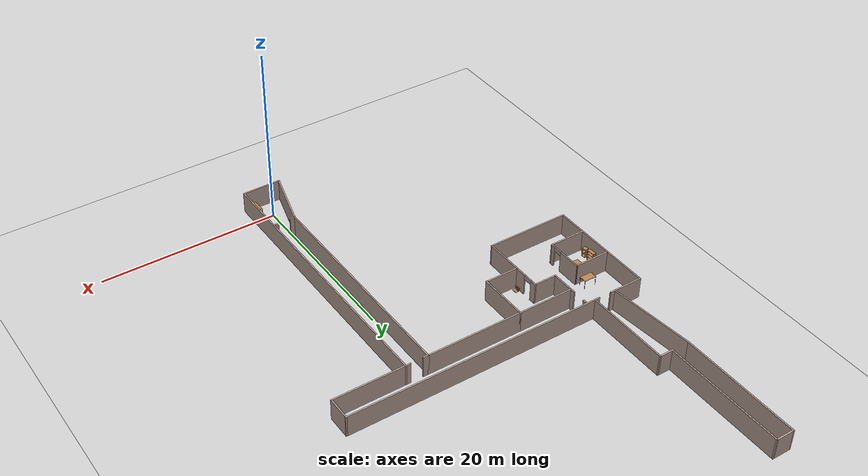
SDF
<sdf version="1.6">
 <world name="default">
  <light name="sun" type="directional">
   <pose>0 0 10 0 -0 0</pose>
   <diffuse>0.8 0.8 0.8 1</diffuse>
   <specular>0.1 0.1 0.1 1</specular>
   <attenuation>
    <range>1000</range>
    <constant>0.9</constant>
    <linear>0.01</linear>
    <quadratic>0.001</quadratic>
   </attenuation>
   <direction>-0.5 0.5 -1</direction>
  </light>
  <model name="ground_plane">
   <static>1</static>
   <link name="link">
    <collision name="collision">
     <geometry><plane><normal>0 0 1</normal><size>100 100</size></plane></geometry>
     <surface><friction><ode><mu>100</mu><mu2>50</mu2></ode></friction></surface>
    </collision>
    <visual name="visual">
     <cast_shadows>0</cast_shadows>
     <geometry><plane><normal>0 0 1</normal><size>100 120</size></plane></geometry>
     <material>
      <script><uri>file://media/materials/scripts/gazebo.material</uri><name>Gazebo/Grey</name></script>
     </material>
    </visual>
   </link>
  </model>
  <gravity>0 0 -9.8</gravity>
  <magnetic_field>6e-06 2.3e-05 -4.2e-05</magnetic_field>
  <atmosphere type="adiabatic"/>
  <physics name="default_physics" default="0" type="ode">
   <max_step_size>0.001</max_step_size>
   <real_time_factor>1</real_time_factor>
   <real_time_update_rate>1000</real_time_update_rate>
  </physics>
  <scene>
   <ambient>0.9 0.9 0.9 1</ambient>
   <background>0.7 0.7 0.7 1</background>
   <shadows>1</shadows>
   <grid>0</grid>
  </scene>
  <spherical_coordinates>
   <surface_model>EARTH_WGS84</surface_model>
   <latitude_deg>0</latitude_deg>
   <longitude_deg>0</longitude_deg>
   <elevation>0</elevation>
   <heading_deg>0</heading_deg>
  </spherical_coordinates>
  <model name="utias2">
   <pose>-6.98603 26.1314 -0.100807 0 -0 0</pose>
   <link name="Wall_0">
    <collision name="Wall_0_Collision">
     <geometry><box><size>4.4 0.15 2.5</size></box></geometry>
     <pose>0 0 1.25 0 -0 0</pose>
    </collision>
    <visual name="Wall_0_Visual">
     <pose>0 0 1.25 0 -0 0</pose>
     <geometry><box><size>4.4 0.15 2.5</size></box></geometry>
     <material>
      <script><uri>file://media/materials/scripts/gazebo.material</uri><name>Gazebo/Grey</name></script>
      <ambient>0.760784 0.662745 0.627451 1</ambient>
     </material>
    </visual>
    <pose>7.00014 -28.4915 0 0 -0 0</pose>
   </link>
   <link name="Wall_1">
    <collision name="Wall_1_Collision">
     <geometry><box><size>31.65 0.15 2.5</size></box></geometry>
     <pose>0 0 1.25 0 -0 0</pose>
    </collision>
    <visual name="Wall_1_Visual">
     <pose>0 0 1.25 0 -0 0</pose>
     <geometry><box><size>31.65 0.15 2.5</size></box></geometry>
     <material>
      <script><uri>file://media/materials/scripts/gazebo.material</uri><name>Gazebo/Grey</name></script>
      <ambient>0.760784 0.662745 0.627451 1</ambient>
     </material>
    </visual>
    <pose>9.12514 -12.7415 0 0 -0 1.5708</pose>
   </link>
   <link name="Wall_10">
    <collision name="Wall_10_Collision">
     <geometry><box><size>9.70249 0.15 2.5</size></box></geometry>
     <pose>0 0 1.25 0 -0 0</pose>
    </collision>
    <visual name="Wall_10_Visual">
     <pose>0 0 1.25 0 -0 0</pose>
     <geometry><box><size>9.70249 0.15 2.5</size></box></geometry>
     <material>
      <script><uri>file://media/materials/scripts/gazebo.material</uri><name>Gazebo/Grey</name></script>
      <ambient>0.760784 0.662745 0.627451 1</ambient>
     </material>
    </visual>
    <pose>-14.3749 10.2585 0 0 0 -1.46592</pose>
   </link>
   <link name="Wall_12">
    <collision name="Wall_12_Collision">
     <geometry><box><size>3.4 0.15 2.5</size></box></geometry>
     <pose>0 0 1.25 0 -0 0</pose>
    </collision>
    <visual name="Wall_12_Visual">
     <pose>0 0 1.25 0 -0 0</pose>
     <geometry><box><size>3.4 0.15 2.5</size></box></geometry>
     <material>
      <script><uri>file://media/materials/scripts/gazebo.material</uri><name>Gazebo/Grey</name></script>
      <ambient>0.760784 0.662745 0.627451 1</ambient>
     </material>
    </visual>
    <pose>-15.4999 5.50846 0 0 -0 3.14159</pose>
   </link>
   <link name="Wall_14">
    <collision name="Wall_14_Collision">
     <geometry><box><size>12.4 0.15 2.5</size></box></geometry>
     <pose>0 0 1.25 0 -0 0</pose>
    </collision>
    <visual name="Wall_14_Visual">
     <pose>0 0 1.25 0 -0 0</pose>
     <geometry><box><size>12.4 0.15 2.5</size></box></geometry>
     <material>
      <script><uri>file://media/materials/scripts/gazebo.material</uri><name>Gazebo/Grey</name></script>
      <ambient>0.760784 0.662745 0.627451 1</ambient>
     </material>
    </visual>
    <pose>-17.1249 -0.616541 0 0 0 -1.5708</pose>
   </link>
   <link name="Wall_15">
    <collision name="Wall_15_Collision">
     <geometry><box><size>9.40054 0.15 2.5</size></box></geometry>
     <pose>0 0 1.25 0 -0 0</pose>
    </collision>
    <visual name="Wall_15_Visual">
     <pose>0 0 1.25 0 -0 0</pose>
     <geometry><box><size>9.40054 0.15 2.5</size></box></geometry>
     <material>
      <script><uri>file://media/materials/scripts/gazebo.material</uri><name>Gazebo/Grey</name></script>
      <ambient>0.760784 0.662745 0.627451 1</ambient>
     </material>
    </visual>
    <pose>-12.4999 -6.74154 0 0 -0 0</pose>
   </link>
   <link name="Wall_16">
    <collision name="Wall_16_Collision">
     <geometry><box><size>4.4 0.15 2.5</size></box></geometry>
     <pose>0 0 1.25 0 -0 0</pose>
    </collision>
    <visual name="Wall_16_Visual">
     <pose>0 0 1.25 0 -0 0</pose>
     <geometry><box><size>4.4 0.15 2.5</size></box></geometry>
     <material>
      <script><uri>file://media/materials/scripts/gazebo.material</uri><name>Gazebo/Grey</name></script>
      <ambient>0.760784 0.662745 0.627451 1</ambient>
     </material>
    </visual>
    <pose>-7.87486 -4.61654 0 0 -0 1.5708</pose>
   </link>
   <link name="Wall_17">
    <collision name="Wall_17_Collision">
     <geometry><box><size>3.9 0.15 2.5</size></box></geometry>
     <pose>0 0 1.25 0 -0 0</pose>
    </collision>
    <visual name="Wall_17_Visual">
     <pose>0 0 1.25 0 -0 0</pose>
     <geometry><box><size>3.9 0.15 2.5</size></box></geometry>
     <material>
      <script><uri>file://media/materials/scripts/gazebo.material</uri><name>Gazebo/Grey</name></script>
      <ambient>0.760784 0.662745 0.627451 1</ambient>
     </material>
    </visual>
    <pose>-5.99986 -2.49154 0 0 -0 0</pose>
   </link>
   <link name="Wall_18">
    <collision name="Wall_18_Collision">
     <geometry><box><size>5.65 0.15 2.5</size></box></geometry>
     <pose>0 0 1.25 0 -0 0</pose>
    </collision>
    <visual name="Wall_18_Visual">
     <pose>0 0 1.25 0 -0 0</pose>
     <geometry><box><size>5.65 0.15 2.5</size></box></geometry>
     <material>
      <script><uri>file://media/materials/scripts/gazebo.material</uri><name>Gazebo/Grey</name></script>
      <ambient>0.760784 0.662745 0.627451 1</ambient>
     </material>
    </visual>
    <pose>-4.12486 0.258459 0 0 -0 1.5708</pose>
   </link>
   <link name="Wall_19">
    <collision name="Wall_19_Collision">
     <geometry><box><size>10.9 0.15 2.5</size></box></geometry>
     <pose>0 0 1.25 0 -0 0</pose>
    </collision>
    <visual name="Wall_19_Visual">
     <pose>0 0 1.25 0 -0 0</pose>
     <geometry><box><size>10.9 0.15 2.5</size></box></geometry>
     <material>
      <script><uri>file://media/materials/scripts/gazebo.material</uri><name>Gazebo/Grey</name></script>
      <ambient>0.760784 0.662745 0.627451 1</ambient>
     </material>
    </visual>
    <pose>1.25014 3.00846 0 0 -0 0</pose>
   </link>
   <link name="Wall_2">
    <collision name="Wall_2_Collision">
     <geometry><box><size>8.15 0.15 2.5</size></box></geometry>
     <pose>0 0 1.25 0 -0 0</pose>
    </collision>
    <visual name="Wall_2_Visual">
     <pose>0 0 1.25 0 -0 0</pose>
     <geometry><box><size>8.15 0.15 2.5</size></box></geometry>
     <material>
      <script><uri>file://media/materials/scripts/gazebo.material</uri><name>Gazebo/Grey</name></script>
      <ambient>0.760784 0.662745 0.627451 1</ambient>
     </material>
    </visual>
    <pose>13.1251 3.00846 0 0 -0 0</pose>
   </link>
   <link name="Wall_21">
    <collision name="Wall_21_Collision">
     <geometry><box><size>6.4 0.15 2.5</size></box></geometry>
     <pose>0 0 1.25 0 -0 0</pose>
    </collision>
    <visual name="Wall_21_Visual">
     <pose>0 0 1.25 0 -0 0</pose>
     <geometry><box><size>6.4 0.15 2.5</size></box></geometry>
     <material>
      <script><uri>file://media/materials/scripts/gazebo.material</uri><name>Gazebo/Grey</name></script>
      <ambient>0.760784 0.662745 0.627451 1</ambient>
     </material>
    </visual>
    <pose>-7.24986 3.00846 0 0 -0 3.14159</pose>
   </link>
   <link name="Wall_22">
    <collision name="Wall_22_Collision">
     <geometry><box><size>2.65 0.15 2.5</size></box></geometry>
     <pose>0 0 1.25 0 -0 0</pose>
    </collision>
    <visual name="Wall_22_Visual">
     <pose>0 0 1.25 0 -0 0</pose>
     <geometry><box><size>2.65 0.15 2.5</size></box></geometry>
     <material>
      <script><uri>file://media/materials/scripts/gazebo.material</uri><name>Gazebo/Grey</name></script>
      <ambient>0.760784 0.662745 0.627451 1</ambient>
     </material>
    </visual>
    <pose>-10.3749 1.75846 0 0 0 -1.5708</pose>
   </link>
   <link name="Wall_23">
    <collision name="Wall_23_Collision">
     <geometry><box><size>2.65 0.15 2.5</size></box></geometry>
     <pose>0 0 1.25 0 -0 0</pose>
    </collision>
    <visual name="Wall_23_Visual">
     <pose>0 0 1.25 0 -0 0</pose>
     <geometry><box><size>2.65 0.15 2.5</size></box></geometry>
     <material>
      <script><uri>file://media/materials/scripts/gazebo.material</uri><name>Gazebo/Grey</name></script>
      <ambient>0.760784 0.662745 0.627451 1</ambient>
     </material>
    </visual>
    <pose>-9.12486 0.508459 0 0 -0 0</pose>
   </link>
   <link name="Wall_24">
    <pose>-7.87486 -0.991541 0 0 0 -1.5708</pose>
    <visual name="Wall_24_Visual_0">
     <pose>-1.20455 0 1.25 0 -0 0</pose>
     <geometry><box><size>0.740907 0.15 2.5</size></box></geometry>
     <material>
      <script><uri>file://media/materials/scripts/gazebo.material</uri><name>Gazebo/Grey</name></script>
      <ambient>0.760784 0.662745 0.627451 1</ambient>
     </material>
    </visual>
    <collision name="Wall_24_Collision_0">
     <geometry><box><size>0.740907 0.15 2.5</size></box></geometry>
     <pose>-1.20455 0 1.25 0 -0 0</pose>
    </collision>
    <visual name="Wall_24_Visual_1">
     <pose>0.870453 0 1.25 0 -0 0</pose>
     <geometry><box><size>1.40909 0.15 2.5</size></box></geometry>
     <material>
      <script><uri>file://media/materials/scripts/gazebo.material</uri><name>Gazebo/Grey</name></script>
      <ambient>0.760784 0.662745 0.627451 1</ambient>
     </material>
    </visual>
    <collision name="Wall_24_Collision_1">
     <geometry><box><size>1.40909 0.15 2.5</size></box></geometry>
     <pose>0.870453 0 1.25 0 -0 0</pose>
    </collision>
    <visual name="Wall_24_Visual_2">
     <pose>-0.334093 0 2.25 0 -0 0</pose>
     <geometry><box><size>1 0.15 0.5</size></box></geometry>
     <material>
      <script><uri>file://media/materials/scripts/gazebo.material</uri><name>Gazebo/Grey</name></script>
      <ambient>0.760784 0.662745 0.627451 1</ambient>
     </material>
    </visual>
    <collision name="Wall_24_Collision_2">
     <geometry><box><size>1 0.15 0.5</size></box></geometry>
     <pose>-0.334093 0 2.25 0 -0 0</pose>
    </collision>
   </link>
   <link name="Wall_26">
    <collision name="Wall_26_Collision">
     <geometry><box><size>4.15 0.15 2.5</size></box></geometry>
     <pose>0 0 1.25 0 -0 0</pose>
    </collision>
    <visual name="Wall_26_Visual">
     <pose>0 0 1.25 0 -0 0</pose>
     <geometry><box><size>4.15 0.15 2.5</size></box></geometry>
     <material>
      <script><uri>file://media/materials/scripts/gazebo.material</uri><name>Gazebo/Grey</name></script>
      <ambient>0.760784 0.662745 0.627451 1</ambient>
     </material>
    </visual>
    <pose>-15.1249 0.508459 0 0 -0 0</pose>
   </link>
   <link name="Wall_27">
    <pose>-13.1249 -1.49154 0 0 0 -1.5708</pose>
    <visual name="Wall_27_Visual_0">
     <pose>-0.771545 0 1.25 0 -0 0</pose>
     <geometry><box><size>2.60691 0.15 2.5</size></box></geometry>
     <material>
      <script><uri>file://media/materials/scripts/gazebo.material</uri><name>Gazebo/Grey</name></script>
      <ambient>0.760784 0.662745 0.627451 1</ambient>
     </material>
    </visual>
    <collision name="Wall_27_Collision_0">
     <geometry><box><size>2.60691 0.15 2.5</size></box></geometry>
     <pose>-0.771545 0 1.25 0 -0 0</pose>
    </collision>
    <visual name="Wall_27_Visual_1">
     <pose>1.80346 0 1.25 0 -0 0</pose>
     <geometry><box><size>0.543089 0.15 2.5</size></box></geometry>
     <material>
      <script><uri>file://media/materials/scripts/gazebo.material</uri><name>Gazebo/Grey</name></script>
      <ambient>0.760784 0.662745 0.627451 1</ambient>
     </material>
    </visual>
    <collision name="Wall_27_Collision_1">
     <geometry><box><size>0.543089 0.15 2.5</size></box></geometry>
     <pose>1.80346 0 1.25 0 -0 0</pose>
    </collision>
    <visual name="Wall_27_Visual_2">
     <pose>1.03191 0 2.25 0 -0 0</pose>
     <geometry><box><size>1 0.15 0.5</size></box></geometry>
     <material>
      <script><uri>file://media/materials/scripts/gazebo.material</uri><name>Gazebo/Grey</name></script>
      <ambient>0.760784 0.662745 0.627451 1</ambient>
     </material>
    </visual>
    <collision name="Wall_27_Collision_2">
     <geometry><box><size>1 0.15 0.5</size></box></geometry>
     <pose>1.03191 0 2.25 0 -0 0</pose>
    </collision>
   </link>
   <link name="Wall_28">
    <collision name="Wall_28_Collision">
     <geometry><box><size>4.15 0.15 2.5</size></box></geometry>
     <pose>0 0 1.25 0 -0 0</pose>
    </collision>
    <visual name="Wall_28_Visual">
     <pose>0 0 1.25 0 -0 0</pose>
     <geometry><box><size>4.15 0.15 2.5</size></box></geometry>
     <material>
      <script><uri>file://media/materials/scripts/gazebo.material</uri><name>Gazebo/Grey</name></script>
      <ambient>0.760784 0.662745 0.627451 1</ambient>
     </material>
    </visual>
    <pose>-15.1249 -3.49154 0 0 -0 3.14159</pose>
   </link>
   <link name="Wall_3">
    <collision name="Wall_3_Collision">
     <geometry><box><size>2.65 0.15 2.5</size></box></geometry>
     <pose>0 0 1.25 0 -0 0</pose>
    </collision>
    <visual name="Wall_3_Visual">
     <pose>0 0 1.25 0 -0 0</pose>
     <geometry><box><size>2.65 0.15 2.5</size></box></geometry>
     <material>
      <script><uri>file://media/materials/scripts/gazebo.material</uri><name>Gazebo/Grey</name></script>
      <ambient>0.760784 0.662745 0.627451 1</ambient>
     </material>
    </visual>
    <pose>17.1251 4.25846 0 0 -0 1.5708</pose>
   </link>
   <link name="Wall_30">
    <collision name="Wall_30_Collision">
     <geometry><box><size>25.15 0.15 2.5</size></box></geometry>
     <pose>0 0 1.25 0 -0 0</pose>
    </collision>
    <visual name="Wall_30_Visual">
     <pose>0 0 1.25 0 -0 0</pose>
     <geometry><box><size>25.15 0.15 2.5</size></box></geometry>
     <material>
      <script><uri>file://media/materials/scripts/gazebo.material</uri><name>Gazebo/Grey</name></script>
      <ambient>0.760784 0.662745 0.627451 1</ambient>
     </material>
    </visual>
    <pose>6.62514 -9.49154 0 0 0 -1.5708</pose>
   </link>
   <link name="Wall_31">
    <collision name="Wall_31_Collision">
     <geometry><box><size>6.88146 0.15 2.5</size></box></geometry>
     <pose>0 0 1.25 0 -0 0</pose>
    </collision>
    <visual name="Wall_31_Visual">
     <pose>0 0 1.25 0 -0 0</pose>
     <geometry><box><size>6.88146 0.15 2.5</size></box></geometry>
     <material>
      <script><uri>file://media/materials/scripts/gazebo.material</uri><name>Gazebo/Grey</name></script>
      <ambient>0.760784 0.662745 0.627451 1</ambient>
     </material>
    </visual>
    <pose>5.75014 -25.2415 0 0 0 -1.83379</pose>
   </link>
   <link name="Wall_33">
    <collision name="Wall_33_Collision">
     <geometry><box><size>0.65 0.15 2.5</size></box></geometry>
     <pose>0 0 1.25 0 -0 0</pose>
    </collision>
    <visual name="Wall_33_Visual">
     <pose>0 0 1.25 0 -0 0</pose>
     <geometry><box><size>0.65 0.15 2.5</size></box></geometry>
     <material>
      <script><uri>file://media/materials/scripts/gazebo.material</uri><name>Gazebo/Grey</name></script>
      <ambient>0.760784 0.662745 0.627451 1</ambient>
     </material>
    </visual>
    <pose>6.87514 -21.9915 0 0 -0 0</pose>
   </link>
   <link name="Wall_35">
    <collision name="Wall_35_Collision">
     <geometry><box><size>0.65 0.15 2.5</size></box></geometry>
     <pose>0 0 1.25 0 -0 0</pose>
    </collision>
    <visual name="Wall_35_Visual">
     <pose>0 0 1.25 0 -0 0</pose>
     <geometry><box><size>0.65 0.15 2.5</size></box></geometry>
     <material>
      <script><uri>file://media/materials/scripts/gazebo.material</uri><name>Gazebo/Grey</name></script>
      <ambient>0.760784 0.662745 0.627451 1</ambient>
     </material>
    </visual>
    <pose>8.87514 -21.9915 0 0 -0 3.14159</pose>
   </link>
   <link name="Wall_37">
    <collision name="Wall_37_Collision">
     <geometry><box><size>0.65 0.15 2.5</size></box></geometry>
     <pose>0 0 1.25 0 -0 0</pose>
    </collision>
    <visual name="Wall_37_Visual">
     <pose>0 0 1.25 0 -0 0</pose>
     <geometry><box><size>0.65 0.15 2.5</size></box></geometry>
     <material>
      <script><uri>file://media/materials/scripts/gazebo.material</uri><name>Gazebo/Grey</name></script>
      <ambient>0.760784 0.662745 0.627451 1</ambient>
     </material>
    </visual>
    <pose>8.87514 3.00846 0 0 -0 3.14159</pose>
   </link>
   <link name="Wall_39">
    <collision name="Wall_39_Collision">
     <geometry><box><size>0.65 0.15 2.5</size></box></geometry>
     <pose>0 0 1.25 0 -0 0</pose>
    </collision>
    <visual name="Wall_39_Visual">
     <pose>0 0 1.25 0 -0 0</pose>
     <geometry><box><size>0.65 0.15 2.5</size></box></geometry>
     <material>
      <script><uri>file://media/materials/scripts/gazebo.material</uri><name>Gazebo/Grey</name></script>
      <ambient>0.760784 0.662745 0.627451 1</ambient>
     </material>
    </visual>
    <pose>6.87514 3.00846 0 0 -0 0</pose>
   </link>
   <link name="Wall_4">
    <collision name="Wall_4_Collision">
     <geometry><box><size>28.65 0.15 2.5</size></box></geometry>
     <pose>0 0 1.25 0 -0 0</pose>
    </collision>
    <visual name="Wall_4_Visual">
     <pose>0 0 1.25 0 -0 0</pose>
     <geometry><box><size>28.65 0.15 2.5</size></box></geometry>
     <material>
      <script><uri>file://media/materials/scripts/gazebo.material</uri><name>Gazebo/Grey</name></script>
      <ambient>0.760784 0.662745 0.627451 1</ambient>
     </material>
    </visual>
    <pose>2.87514 5.50846 0 0 -0 3.14159</pose>
   </link>
   <link name="Wall_41">
    <collision name="Wall_41_Collision">
     <geometry><box><size>0.65 0.15 2.5</size></box></geometry>
     <pose>0 0 1.25 0 -0 0</pose>
    </collision>
    <visual name="Wall_41_Visual">
     <pose>0 0 1.25 0 -0 0</pose>
     <geometry><box><size>0.65 0.15 2.5</size></box></geometry>
     <material>
      <script><uri>file://media/materials/scripts/gazebo.material</uri><name>Gazebo/Grey</name></script>
      <ambient>0.760784 0.662745 0.627451 1</ambient>
     </material>
    </visual>
    <pose>-10.3749 3.25846 0 0 -0 1.5708</pose>
   </link>
   <link name="Wall_43">
    <collision name="Wall_43_Collision">
     <geometry><box><size>0.65 0.15 2.5</size></box></geometry>
     <pose>0 0 1.25 0 -0 0</pose>
    </collision>
    <visual name="Wall_43_Visual">
     <pose>0 0 1.25 0 -0 0</pose>
     <geometry><box><size>0.65 0.15 2.5</size></box></geometry>
     <material>
      <script><uri>file://media/materials/scripts/gazebo.material</uri><name>Gazebo/Grey</name></script>
      <ambient>0.760784 0.662745 0.627451 1</ambient>
     </material>
    </visual>
    <pose>-10.3749 5.25846 0 0 0 -1.5708</pose>
   </link>
   <link name="Wall_45">
    <collision name="Wall_45_Collision">
     <geometry><box><size>0.65 0.15 2.5</size></box></geometry>
     <pose>0 0 1.25 0 -0 0</pose>
    </collision>
    <visual name="Wall_45_Visual">
     <pose>0 0 1.25 0 -0 0</pose>
     <geometry><box><size>0.65 0.15 2.5</size></box></geometry>
     <material>
      <script><uri>file://media/materials/scripts/gazebo.material</uri><name>Gazebo/Grey</name></script>
      <ambient>0.760784 0.662745 0.627451 1</ambient>
     </material>
    </visual>
    <pose>-11.6249 5.50846 0 0 -0 3.14159</pose>
   </link>
   <link name="Wall_47">
    <collision name="Wall_47_Collision">
     <geometry><box><size>0.65 0.15 2.5</size></box></geometry>
     <pose>0 0 1.25 0 -0 0</pose>
    </collision>
    <visual name="Wall_47_Visual">
     <pose>0 0 1.25 0 -0 0</pose>
     <geometry><box><size>0.65 0.15 2.5</size></box></geometry>
     <material>
      <script><uri>file://media/materials/scripts/gazebo.material</uri><name>Gazebo/Grey</name></script>
      <ambient>0.760784 0.662745 0.627451 1</ambient>
     </material>
    </visual>
    <pose>-13.6249 5.50846 0 0 -0 0</pose>
   </link>
   <link name="Wall_5">
    <collision name="Wall_5_Collision">
     <geometry><box><size>9.65 0.15 2.5</size></box></geometry>
     <pose>0 0 1.25 0 -0 0</pose>
    </collision>
    <visual name="Wall_5_Visual">
     <pose>0 0 1.25 0 -0 0</pose>
     <geometry><box><size>9.65 0.15 2.5</size></box></geometry>
     <material>
      <script><uri>file://media/materials/scripts/gazebo.material</uri><name>Gazebo/Grey</name></script>
      <ambient>0.760784 0.662745 0.627451 1</ambient>
     </material>
    </visual>
    <pose>-11.3749 10.2585 0 0 -0 1.5708</pose>
   </link>
   <link name="Wall_6">
    <collision name="Wall_6_Collision">
     <geometry><box><size>1.65 0.15 2.5</size></box></geometry>
     <pose>0 0 1.25 0 -0 0</pose>
    </collision>
    <visual name="Wall_6_Visual">
     <pose>0 0 1.25 0 -0 0</pose>
     <geometry><box><size>1.65 0.15 2.5</size></box></geometry>
     <material>
      <script><uri>file://media/materials/scripts/gazebo.material</uri><name>Gazebo/Grey</name></script>
      <ambient>0.760784 0.662745 0.627451 1</ambient>
     </material>
    </visual>
    <pose>-12.1249 15.0085 0 0 -0 3.14159</pose>
   </link>
   <link name="Wall_7">
    <collision name="Wall_7_Collision">
     <geometry><box><size>13.65 0.15 2.5</size></box></geometry>
     <pose>0 0 1.25 0 -0 0</pose>
    </collision>
    <visual name="Wall_7_Visual">
     <pose>0 0 1.25 0 -0 0</pose>
     <geometry><box><size>13.65 0.15 2.5</size></box></geometry>
     <material>
      <script><uri>file://media/materials/scripts/gazebo.material</uri><name>Gazebo/Grey</name></script>
      <ambient>0.760784 0.662745 0.627451 1</ambient>
     </material>
    </visual>
    <pose>-12.8749 21.7585 0 0 -0 1.5708</pose>
   </link>
   <link name="Wall_8">
    <collision name="Wall_8_Collision">
     <geometry><box><size>2.15 0.15 2.5</size></box></geometry>
     <pose>0 0 1.25 0 -0 0</pose>
    </collision>
    <visual name="Wall_8_Visual">
     <pose>0 0 1.25 0 -0 0</pose>
     <geometry><box><size>2.15 0.15 2.5</size></box></geometry>
     <material>
      <script><uri>file://media/materials/scripts/gazebo.material</uri><name>Gazebo/Grey</name></script>
      <ambient>0.760784 0.662745 0.627451 1</ambient>
     </material>
    </visual>
    <pose>-13.8749 28.5085 0 0 -0 3.14159</pose>
   </link>
   <link name="Wall_9">
    <collision name="Wall_9_Collision">
     <geometry><box><size>13.65 0.15 2.5</size></box></geometry>
     <pose>0 0 1.25 0 -0 0</pose>
    </collision>
    <visual name="Wall_9_Visual">
     <pose>0 0 1.25 0 -0 0</pose>
     <geometry><box><size>13.65 0.15 2.5</size></box></geometry>
     <material>
      <script><uri>file://media/materials/scripts/gazebo.material</uri><name>Gazebo/Grey</name></script>
      <ambient>0.760784 0.662745 0.627451 1</ambient>
     </material>
    </visual>
    <pose>-14.8749 21.7585 0 0 0 -1.5708</pose>
   </link>
   <static>1</static>
  </model>
  <model name="table">
   <static>0</static>
   <link name="link">
    <collision name="surface">
     <pose>0 0 1 0 -0 0</pose>
     <geometry><box><size>1.5 0.8 0.03</size></box></geometry>
     <surface><friction><ode><mu>0.6</mu><mu2>0.6</mu2></ode></friction></surface>
    </collision>
    <visual name="visual1">
     <pose>0 0 1 0 -0 0</pose>
     <geometry><box><size>1.4 0.8 0.04</size></box></geometry>
     <material>
      <script><uri>file://media/materials/scripts/gazebo.material</uri><name>Gazebo/Wood</name></script>
     </material>
    </visual>
    <collision name="front_left_leg">
     <pose>0.68 0.38 0.5 0 -0 0</pose>
     <geometry><cylinder><radius>0.02</radius><length>1</length></cylinder></geometry>
    </collision>
    <visual name="front_left_leg">
     <pose>0.68 0.38 0.5 0 -0 0</pose>
     <geometry><cylinder><radius>0.02</radius><length>1</length></cylinder></geometry>
     <material>
      <script><uri>file://media/materials/scripts/gazebo.material</uri><name>Gazebo/Grey</name></script>
     </material>
    </visual>
    <collision name="front_right_leg">
     <pose>0.68 -0.38 0.5 0 -0 0</pose>
     <geometry><cylinder><radius>0.02</radius><length>1</length></cylinder></geometry>
    </collision>
    <visual name="front_right_leg">
     <pose>0.68 -0.38 0.5 0 -0 0</pose>
     <geometry><cylinder><radius>0.02</radius><length>1</length></cylinder></geometry>
     <material>
      <script><uri>file://media/materials/scripts/gazebo.material</uri><name>Gazebo/Grey</name></script>
     </material>
    </visual>
    <collision name="back_right_leg">
     <pose>-0.68 -0.38 0.5 0 -0 0</pose>
     <geometry><cylinder><radius>0.02</radius><length>1</length></cylinder></geometry>
    </collision>
    <visual name="back_right_leg">
     <pose>-0.68 -0.38 0.5 0 -0 0</pose>
     <geometry><cylinder><radius>0.02</radius><length>1</length></cylinder></geometry>
     <material>
      <script><uri>file://media/materials/scripts/gazebo.material</uri><name>Gazebo/Grey</name></script>
     </material>
    </visual>
    <collision name="back_left_leg">
     <pose>-0.68 0.38 0.5 0 -0 0</pose>
     <geometry><cylinder><radius>0.02</radius><length>1</length></cylinder></geometry>
    </collision>
    <visual name="back_left_leg">
     <pose>-0.68 0.38 0.5 0 -0 0</pose>
     <geometry><cylinder><radius>0.02</radius><length>1</length></cylinder></geometry>
     <material>
      <script><uri>file://media/materials/scripts/gazebo.material</uri><name>Gazebo/Grey</name></script>
     </material>
    </visual>
    <inertial>
     <inertia><ixx>1</ixx><ixy>0</ixy><ixz>0</ixz><iyy>1</iyy><iyz>0</iyz><izz>1</izz></inertia>
     <mass>1</mass>
    </inertial>
   </link>
   <pose>1.40885 -1.2425 -4e-06 -2e-06 5e-06 -1.57252</pose>
  </model>
  <model name="table_0">
   <static>0</static>
   <link name="link">
    <collision name="surface">
     <pose>0 0 1 0 -0 0</pose>
     <geometry><box><size>1.5 0.8 0.03</size></box></geometry>
     <surface><friction><ode><mu>0.6</mu><mu2>0.6</mu2></ode></friction></surface>
    </collision>
    <visual name="visual1">
     <pose>0 0 1 0 -0 0</pose>
     <geometry><box><size>1.4 0.8 0.04</size></box></geometry>
     <material>
      <script><uri>file://media/materials/scripts/gazebo.material</uri><name>Gazebo/Wood</name></script>
     </material>
    </visual>
    <collision name="front_left_leg">
     <pose>0.68 0.38 0.5 0 -0 0</pose>
     <geometry><cylinder><radius>0.02</radius><length>1</length></cylinder></geometry>
    </collision>
    <visual name="front_left_leg">
     <pose>0.68 0.38 0.5 0 -0 0</pose>
     <geometry><cylinder><radius>0.02</radius><length>1</length></cylinder></geometry>
     <material>
      <script><uri>file://media/materials/scripts/gazebo.material</uri><name>Gazebo/Grey</name></script>
     </material>
    </visual>
    <collision name="front_right_leg">
     <pose>0.68 -0.38 0.5 0 -0 0</pose>
     <geometry><cylinder><radius>0.02</radius><length>1</length></cylinder></geometry>
    </collision>
    <visual name="front_right_leg">
     <pose>0.68 -0.38 0.5 0 -0 0</pose>
     <geometry><cylinder><radius>0.02</radius><length>1</length></cylinder></geometry>
     <material>
      <script><uri>file://media/materials/scripts/gazebo.material</uri><name>Gazebo/Grey</name></script>
     </material>
    </visual>
    <collision name="back_right_leg">
     <pose>-0.68 -0.38 0.5 0 -0 0</pose>
     <geometry><cylinder><radius>0.02</radius><length>1</length></cylinder></geometry>
    </collision>
    <visual name="back_right_leg">
     <pose>-0.68 -0.38 0.5 0 -0 0</pose>
     <geometry><cylinder><radius>0.02</radius><length>1</length></cylinder></geometry>
     <material>
      <script><uri>file://media/materials/scripts/gazebo.material</uri><name>Gazebo/Grey</name></script>
     </material>
    </visual>
    <collision name="back_left_leg">
     <pose>-0.68 0.38 0.5 0 -0 0</pose>
     <geometry><cylinder><radius>0.02</radius><length>1</length></cylinder></geometry>
    </collision>
    <visual name="back_left_leg">
     <pose>-0.68 0.38 0.5 0 -0 0</pose>
     <geometry><cylinder><radius>0.02</radius><length>1</length></cylinder></geometry>
     <material>
      <script><uri>file://media/materials/scripts/gazebo.material</uri><name>Gazebo/Grey</name></script>
     </material>
    </visual>
    <inertial>
     <inertia><ixx>1</ixx><ixy>0</ixy><ixz>0</ixz><iyy>1</iyy><iyz>0</iyz><izz>1</izz></inertia>
     <mass>1</mass>
    </inertial>
   </link>
   <pose>-21.2383 25.0678 -9e-06 -1e-06 0 0</pose>
  </model>
  <model name="bookshelf">
   <static>1</static>
   <link name="link">
    <inertial><mass>1</mass></inertial>
    <collision name="back">
     <pose>0 0.005 0.6 0 -0 0</pose>
     <geometry><box><size>0.9 0.01 1.2</size></box></geometry>
    </collision>
    <visual name="visual1">
     <pose>0 0.005 0.6 0 -0 0</pose>
     <geometry><box><size>0.9 0.01 1.2</size></box></geometry>
     <material>
      <script><uri>file://media/materials/scripts/gazebo.material</uri><name>Gazebo/Wood</name></script>
     </material>
    </visual>
    <collision name="left_side">
     <pose>0.45 -0.195 0.6 0 -0 0</pose>
     <geometry><box><size>0.02 0.4 1.2</size></box></geometry>
    </collision>
    <visual name="visual2">
     <pose>0.45 -0.195 0.6 0 -0 0</pose>
     <geometry><box><size>0.02 0.4 1.2</size></box></geometry>
     <material>
      <script><uri>file://media/materials/scripts/gazebo.material</uri><name>Gazebo/Wood</name></script>
     </material>
    </visual>
    <collision name="right_side">
     <pose>-0.45 -0.195 0.6 0 -0 0</pose>
     <geometry><box><size>0.02 0.4 1.2</size></box></geometry>
    </collision>
    <visual name="visual3">
     <pose>-0.45 -0.195 0.6 0 -0 0</pose>
     <geometry><box><size>0.02 0.4 1.2</size></box></geometry>
     <material>
      <script><uri>file://media/materials/scripts/gazebo.material</uri><name>Gazebo/Wood</name></script>
     </material>
    </visual>
    <collision name="bottom">
     <pose>0 -0.195 0.03 0 -0 0</pose>
     <geometry><box><size>0.88 0.4 0.06</size></box></geometry>
    </collision>
    <visual name="visual4">
     <pose>0 -0.195 0.03 0 -0 0</pose>
     <geometry><box><size>0.88 0.4 0.06</size></box></geometry>
     <material>
      <script><uri>file://media/materials/scripts/gazebo.material</uri><name>Gazebo/Wood</name></script>
     </material>
    </visual>
    <collision name="top">
     <pose>0 -0.195 1.19 0 -0 0</pose>
     <geometry><box><size>0.88 0.4 0.02</size></box></geometry>
    </collision>
    <visual name="visual5">
     <pose>0 -0.195 1.19 0 -0 0</pose>
     <geometry><box><size>0.88 0.4 0.02</size></box></geometry>
     <material>
      <script><uri>file://media/materials/scripts/gazebo.material</uri><name>Gazebo/Wood</name></script>
     </material>
    </visual>
    <collision name="low_shelf">
     <pose>0 -0.195 0.43 0 -0 0</pose>
     <geometry><box><size>0.88 0.4 0.02</size></box></geometry>
    </collision>
    <visual name="visual6">
     <pose>0 -0.195 0.43 0 -0 0</pose>
     <geometry><box><size>0.88 0.4 0.02</size></box></geometry>
     <material>
      <script><uri>file://media/materials/scripts/gazebo.material</uri><name>Gazebo/Wood</name></script>
     </material>
    </visual>
    <collision name="high_shelf">
     <pose>0 -0.195 0.8 0 -0 0</pose>
     <geometry><box><size>0.88 0.4 0.02</size></box></geometry>
    </collision>
    <visual name="visual7">
     <pose>0 -0.195 0.8 0 -0 0</pose>
     <geometry><box><size>0.88 0.4 0.02</size></box></geometry>
     <material>
      <script><uri>file://media/materials/scripts/gazebo.material</uri><name>Gazebo/Wood</name></script>
     </material>
    </visual>
   </link>
   <pose>-23.9559 24.7006 0 0 -0 1.60029</pose>
  </model>
  <model name="cabinet">
   <static>1</static>
   <link name="cabinet_bottom_plate">
    <inertial>
     <pose>0 0 -1 0 -0 0</pose>
     <inertia><ixx>2.05</ixx><ixy>0</ixy><ixz>0</ixz><iyy>2.05</iyy><iyz>0</iyz><izz>2.05</izz></inertia>
     <mass>25</mass>
    </inertial>
    <collision name="cabinet_bottom_plate_geom">
     <pose>0 0 0.01 0 -0 0</pose>
     <geometry><box><size>0.45 0.45 0.02</size></box></geometry>
    </collision>
    <visual name="cabinet_bottom_plate_geom_visual">
     <pose>0 0 0.01 0 -0 0</pose>
     <geometry><box><size>0.45 0.45 0.02</size></box></geometry>
     <material>
      <script><uri>file://media/materials/scripts/gazebo.material</uri><name>Gazebo/Wood</name></script>
     </material>
    </visual>
    <collision name="cabinet_bottom_plate_geom_cabinet_back_plate">
     <pose>0.235 0 0.51 0 -0 0</pose>
     <geometry><box><size>0.02 0.45 1.02</size></box></geometry>
    </collision>
    <visual name="cabinet_bottom_plate_geom_cabinet_back_plate_visual">
     <pose>0.235 0 0.51 0 -0 0</pose>
     <geometry><box><size>0.02 0.45 1.02</size></box></geometry>
     <material>
      <script><uri>file://media/materials/scripts/gazebo.material</uri><name>Gazebo/Wood</name></script>
     </material>
    </visual>
    <collision name="cabinet_bottom_plate_geom_cabinet_left_plate">
     <pose>0 0.235 0.51 0 -0 0</pose>
     <geometry><box><size>0.45 0.02 1.02</size></box></geometry>
    </collision>
    <visual name="cabinet_bottom_plate_geom_cabinet_left_plate_visual">
     <pose>0 0.235 0.51 0 -0 0</pose>
     <geometry><box><size>0.45 0.02 1.02</size></box></geometry>
     <material>
      <script><uri>file://media/materials/scripts/gazebo.material</uri><name>Gazebo/Wood</name></script>
     </material>
    </visual>
    <collision name="cabinet_bottom_plate_geom_cabinet_middle_plate">
     <pose>0 0 0.51 0 -0 0</pose>
     <geometry><box><size>0.45 0.45 0.02</size></box></geometry>
    </collision>
    <visual name="cabinet_bottom_plate_geom_cabinet_middle_plate_visual">
     <pose>0 0 0.51 0 -0 0</pose>
     <geometry><box><size>0.45 0.45 0.02</size></box></geometry>
     <material>
      <script><uri>file://media/materials/scripts/gazebo.material</uri><name>Gazebo/Wood</name></script>
     </material>
    </visual>
    <collision name="cabinet_bottom_plate_geom_cabinet_right_plate">
     <pose>0 -0.235 0.51 0 -0 0</pose>
     <geometry><box><size>0.45 0.02 1.02</size></box></geometry>
    </collision>
    <visual name="cabinet_bottom_plate_geom_cabinet_right_plate_visual">
     <pose>0 -0.235 0.51 0 -0 0</pose>
     <geometry><box><size>0.45 0.02 1.02</size></box></geometry>
     <material>
      <script><uri>file://media/materials/scripts/gazebo.material</uri><name>Gazebo/Wood</name></script>
     </material>
    </visual>
    <collision name="cabinet_bottom_plate_geom_cabinet_top_plate">
     <pose>0 0 1.01 0 -0 0</pose>
     <geometry><box><size>0.45 0.45 0.02</size></box></geometry>
    </collision>
    <visual name="cabinet_bottom_plate_geom_cabinet_top_plate_visual">
     <pose>0 0 1.01 0 -0 0</pose>
     <geometry><box><size>0.45 0.45 0.02</size></box></geometry>
     <material>
      <script><uri>file://media/materials/scripts/gazebo.material</uri><name>Gazebo/Wood</name></script>
     </material>
    </visual>
   </link>
   <pose>-23.7337 23.732 0 0 0 -3.10151</pose>
  </model>
  <model name="bookshelf_0">
   <static>1</static>
   <link name="link">
    <inertial><mass>1</mass></inertial>
    <collision name="back">
     <pose>0 0.005 0.6 0 -0 0</pose>
     <geometry><box><size>0.9 0.01 1.2</size></box></geometry>
    </collision>
    <visual name="visual1">
     <pose>0 0.005 0.6 0 -0 0</pose>
     <geometry><box><size>0.9 0.01 1.2</size></box></geometry>
     <material>
      <script><uri>file://media/materials/scripts/gazebo.material</uri><name>Gazebo/Wood</name></script>
     </material>
    </visual>
    <collision name="left_side">
     <pose>0.45 -0.195 0.6 0 -0 0</pose>
     <geometry><box><size>0.02 0.4 1.2</size></box></geometry>
    </collision>
    <visual name="visual2">
     <pose>0.45 -0.195 0.6 0 -0 0</pose>
     <geometry><box><size>0.02 0.4 1.2</size></box></geometry>
     <material>
      <script><uri>file://media/materials/scripts/gazebo.material</uri><name>Gazebo/Wood</name></script>
     </material>
    </visual>
    <collision name="right_side">
     <pose>-0.45 -0.195 0.6 0 -0 0</pose>
     <geometry><box><size>0.02 0.4 1.2</size></box></geometry>
    </collision>
    <visual name="visual3">
     <pose>-0.45 -0.195 0.6 0 -0 0</pose>
     <geometry><box><size>0.02 0.4 1.2</size></box></geometry>
     <material>
      <script><uri>file://media/materials/scripts/gazebo.material</uri><name>Gazebo/Wood</name></script>
     </material>
    </visual>
    <collision name="bottom">
     <pose>0 -0.195 0.03 0 -0 0</pose>
     <geometry><box><size>0.88 0.4 0.06</size></box></geometry>
    </collision>
    <visual name="visual4">
     <pose>0 -0.195 0.03 0 -0 0</pose>
     <geometry><box><size>0.88 0.4 0.06</size></box></geometry>
     <material>
      <script><uri>file://media/materials/scripts/gazebo.material</uri><name>Gazebo/Wood</name></script>
     </material>
    </visual>
    <collision name="top">
     <pose>0 -0.195 1.19 0 -0 0</pose>
     <geometry><box><size>0.88 0.4 0.02</size></box></geometry>
    </collision>
    <visual name="visual5">
     <pose>0 -0.195 1.19 0 -0 0</pose>
     <geometry><box><size>0.88 0.4 0.02</size></box></geometry>
     <material>
      <script><uri>file://media/materials/scripts/gazebo.material</uri><name>Gazebo/Wood</name></script>
     </material>
    </visual>
    <collision name="low_shelf">
     <pose>0 -0.195 0.43 0 -0 0</pose>
     <geometry><box><size>0.88 0.4 0.02</size></box></geometry>
    </collision>
    <visual name="visual6">
     <pose>0 -0.195 0.43 0 -0 0</pose>
     <geometry><box><size>0.88 0.4 0.02</size></box></geometry>
     <material>
      <script><uri>file://media/materials/scripts/gazebo.material</uri><name>Gazebo/Wood</name></script>
     </material>
    </visual>
    <collision name="high_shelf">
     <pose>0 -0.195 0.8 0 -0 0</pose>
     <geometry><box><size>0.88 0.4 0.02</size></box></geometry>
    </collision>
    <visual name="visual7">
     <pose>0 -0.195 0.8 0 -0 0</pose>
     <geometry><box><size>0.88 0.4 0.02</size></box></geometry>
     <material>
      <script><uri>file://media/materials/scripts/gazebo.material</uri><name>Gazebo/Wood</name></script>
     </material>
    </visual>
   </link>
   <pose>-23.9396 25.9448 0 0 -0 1.575</pose>
  </model>
  <model name="bookshelf_1">
   <static>1</static>
   <link name="link">
    <inertial><mass>1</mass></inertial>
    <collision name="back">
     <pose>0 0.005 0.6 0 -0 0</pose>
     <geometry><box><size>0.9 0.01 1.2</size></box></geometry>
    </collision>
    <visual name="visual1">
     <pose>0 0.005 0.6 0 -0 0</pose>
     <geometry><box><size>0.9 0.01 1.2</size></box></geometry>
     <material>
      <script><uri>file://media/materials/scripts/gazebo.material</uri><name>Gazebo/Wood</name></script>
     </material>
    </visual>
    <collision name="left_side">
     <pose>0.45 -0.195 0.6 0 -0 0</pose>
     <geometry><box><size>0.02 0.4 1.2</size></box></geometry>
    </collision>
    <visual name="visual2">
     <pose>0.45 -0.195 0.6 0 -0 0</pose>
     <geometry><box><size>0.02 0.4 1.2</size></box></geometry>
     <material>
      <script><uri>file://media/materials/scripts/gazebo.material</uri><name>Gazebo/Wood</name></script>
     </material>
    </visual>
    <collision name="right_side">
     <pose>-0.45 -0.195 0.6 0 -0 0</pose>
     <geometry><box><size>0.02 0.4 1.2</size></box></geometry>
    </collision>
    <visual name="visual3">
     <pose>-0.45 -0.195 0.6 0 -0 0</pose>
     <geometry><box><size>0.02 0.4 1.2</size></box></geometry>
     <material>
      <script><uri>file://media/materials/scripts/gazebo.material</uri><name>Gazebo/Wood</name></script>
     </material>
    </visual>
    <collision name="bottom">
     <pose>0 -0.195 0.03 0 -0 0</pose>
     <geometry><box><size>0.88 0.4 0.06</size></box></geometry>
    </collision>
    <visual name="visual4">
     <pose>0 -0.195 0.03 0 -0 0</pose>
     <geometry><box><size>0.88 0.4 0.06</size></box></geometry>
     <material>
      <script><uri>file://media/materials/scripts/gazebo.material</uri><name>Gazebo/Wood</name></script>
     </material>
    </visual>
    <collision name="top">
     <pose>0 -0.195 1.19 0 -0 0</pose>
     <geometry><box><size>0.88 0.4 0.02</size></box></geometry>
    </collision>
    <visual name="visual5">
     <pose>0 -0.195 1.19 0 -0 0</pose>
     <geometry><box><size>0.88 0.4 0.02</size></box></geometry>
     <material>
      <script><uri>file://media/materials/scripts/gazebo.material</uri><name>Gazebo/Wood</name></script>
     </material>
    </visual>
    <collision name="low_shelf">
     <pose>0 -0.195 0.43 0 -0 0</pose>
     <geometry><box><size>0.88 0.4 0.02</size></box></geometry>
    </collision>
    <visual name="visual6">
     <pose>0 -0.195 0.43 0 -0 0</pose>
     <geometry><box><size>0.88 0.4 0.02</size></box></geometry>
     <material>
      <script><uri>file://media/materials/scripts/gazebo.material</uri><name>Gazebo/Wood</name></script>
     </material>
    </visual>
    <collision name="high_shelf">
     <pose>0 -0.195 0.8 0 -0 0</pose>
     <geometry><box><size>0.88 0.4 0.02</size></box></geometry>
    </collision>
    <visual name="visual7">
     <pose>0 -0.195 0.8 0 -0 0</pose>
     <geometry><box><size>0.88 0.4 0.02</size></box></geometry>
     <material>
      <script><uri>file://media/materials/scripts/gazebo.material</uri><name>Gazebo/Wood</name></script>
     </material>
    </visual>
   </link>
   <pose>-13.4786 29.0069 0 0 -0 0</pose>
  </model>
  <model name="bookshelf_2">
   <static>1</static>
   <link name="link">
    <inertial><mass>1</mass></inertial>
    <collision name="back">
     <pose>0 0.005 0.6 0 -0 0</pose>
     <geometry><box><size>0.9 0.01 1.2</size></box></geometry>
    </collision>
    <visual name="visual1">
     <pose>0 0.005 0.6 0 -0 0</pose>
     <geometry><box><size>0.9 0.01 1.2</size></box></geometry>
     <material>
      <script><uri>file://media/materials/scripts/gazebo.material</uri><name>Gazebo/Wood</name></script>
     </material>
    </visual>
    <collision name="left_side">
     <pose>0.45 -0.195 0.6 0 -0 0</pose>
     <geometry><box><size>0.02 0.4 1.2</size></box></geometry>
    </collision>
    <visual name="visual2">
     <pose>0.45 -0.195 0.6 0 -0 0</pose>
     <geometry><box><size>0.02 0.4 1.2</size></box></geometry>
     <material>
      <script><uri>file://media/materials/scripts/gazebo.material</uri><name>Gazebo/Wood</name></script>
     </material>
    </visual>
    <collision name="right_side">
     <pose>-0.45 -0.195 0.6 0 -0 0</pose>
     <geometry><box><size>0.02 0.4 1.2</size></box></geometry>
    </collision>
    <visual name="visual3">
     <pose>-0.45 -0.195 0.6 0 -0 0</pose>
     <geometry><box><size>0.02 0.4 1.2</size></box></geometry>
     <material>
      <script><uri>file://media/materials/scripts/gazebo.material</uri><name>Gazebo/Wood</name></script>
     </material>
    </visual>
    <collision name="bottom">
     <pose>0 -0.195 0.03 0 -0 0</pose>
     <geometry><box><size>0.88 0.4 0.06</size></box></geometry>
    </collision>
    <visual name="visual4">
     <pose>0 -0.195 0.03 0 -0 0</pose>
     <geometry><box><size>0.88 0.4 0.06</size></box></geometry>
     <material>
      <script><uri>file://media/materials/scripts/gazebo.material</uri><name>Gazebo/Wood</name></script>
     </material>
    </visual>
    <collision name="top">
     <pose>0 -0.195 1.19 0 -0 0</pose>
     <geometry><box><size>0.88 0.4 0.02</size></box></geometry>
    </collision>
    <visual name="visual5">
     <pose>0 -0.195 1.19 0 -0 0</pose>
     <geometry><box><size>0.88 0.4 0.02</size></box></geometry>
     <material>
      <script><uri>file://media/materials/scripts/gazebo.material</uri><name>Gazebo/Wood</name></script>
     </material>
    </visual>
    <collision name="low_shelf">
     <pose>0 -0.195 0.43 0 -0 0</pose>
     <geometry><box><size>0.88 0.4 0.02</size></box></geometry>
    </collision>
    <visual name="visual6">
     <pose>0 -0.195 0.43 0 -0 0</pose>
     <geometry><box><size>0.88 0.4 0.02</size></box></geometry>
     <material>
      <script><uri>file://media/materials/scripts/gazebo.material</uri><name>Gazebo/Wood</name></script>
     </material>
    </visual>
    <collision name="high_shelf">
     <pose>0 -0.195 0.8 0 -0 0</pose>
     <geometry><box><size>0.88 0.4 0.02</size></box></geometry>
    </collision>
    <visual name="visual7">
     <pose>0 -0.195 0.8 0 -0 0</pose>
     <geometry><box><size>0.88 0.4 0.02</size></box></geometry>
     <material>
      <script><uri>file://media/materials/scripts/gazebo.material</uri><name>Gazebo/Wood</name></script>
     </material>
    </visual>
   </link>
   <pose>-15.1763 29.0574 0 0 -0 0</pose>
  </model>
  <model name="table_1">
   <static>0</static>
   <link name="link">
    <collision name="surface">
     <pose>0 0 1 0 -0 0</pose>
     <geometry><box><size>1.5 0.8 0.03</size></box></geometry>
     <surface><friction><ode><mu>0.6</mu><mu2>0.6</mu2></ode></friction></surface>
    </collision>
    <visual name="visual1">
     <pose>0 0 1 0 -0 0</pose>
     <geometry><box><size>1.4 0.8 0.04</size></box></geometry>
     <material>
      <script><uri>file://media/materials/scripts/gazebo.material</uri><name>Gazebo/Wood</name></script>
     </material>
    </visual>
    <collision name="front_left_leg">
     <pose>0.68 0.38 0.5 0 -0 0</pose>
     <geometry><cylinder><radius>0.02</radius><length>1</length></cylinder></geometry>
    </collision>
    <visual name="front_left_leg">
     <pose>0.68 0.38 0.5 0 -0 0</pose>
     <geometry><cylinder><radius>0.02</radius><length>1</length></cylinder></geometry>
     <material>
      <script><uri>file://media/materials/scripts/gazebo.material</uri><name>Gazebo/Grey</name></script>
     </material>
    </visual>
    <collision name="front_right_leg">
     <pose>0.68 -0.38 0.5 0 -0 0</pose>
     <geometry><cylinder><radius>0.02</radius><length>1</length></cylinder></geometry>
    </collision>
    <visual name="front_right_leg">
     <pose>0.68 -0.38 0.5 0 -0 0</pose>
     <geometry><cylinder><radius>0.02</radius><length>1</length></cylinder></geometry>
     <material>
      <script><uri>file://media/materials/scripts/gazebo.material</uri><name>Gazebo/Grey</name></script>
     </material>
    </visual>
    <collision name="back_right_leg">
     <pose>-0.68 -0.38 0.5 0 -0 0</pose>
     <geometry><cylinder><radius>0.02</radius><length>1</length></cylinder></geometry>
    </collision>
    <visual name="back_right_leg">
     <pose>-0.68 -0.38 0.5 0 -0 0</pose>
     <geometry><cylinder><radius>0.02</radius><length>1</length></cylinder></geometry>
     <material>
      <script><uri>file://media/materials/scripts/gazebo.material</uri><name>Gazebo/Grey</name></script>
     </material>
    </visual>
    <collision name="back_left_leg">
     <pose>-0.68 0.38 0.5 0 -0 0</pose>
     <geometry><cylinder><radius>0.02</radius><length>1</length></cylinder></geometry>
    </collision>
    <visual name="back_left_leg">
     <pose>-0.68 0.38 0.5 0 -0 0</pose>
     <geometry><cylinder><radius>0.02</radius><length>1</length></cylinder></geometry>
     <material>
      <script><uri>file://media/materials/scripts/gazebo.material</uri><name>Gazebo/Grey</name></script>
     </material>
    </visual>
    <inertial>
     <inertia><ixx>1</ixx><ixy>0</ixy><ixz>0</ixz><iyy>1</iyy><iyz>0</iyz><izz>1</izz></inertia>
     <mass>1</mass>
    </inertial>
   </link>
   <pose>-21.0659 27.4242 0 0 -0 0</pose>
  </model>
  <model name="table_2">
   <static>0</static>
   <link name="link">
    <collision name="surface">
     <pose>0 0 1 0 -0 0</pose>
     <geometry><box><size>1.5 0.8 0.03</size></box></geometry>
     <surface><friction><ode><mu>0.6</mu><mu2>0.6</mu2></ode></friction></surface>
    </collision>
    <visual name="visual1">
     <pose>0 0 1 0 -0 0</pose>
     <geometry><box><size>1.4 0.8 0.04</size></box></geometry>
     <material>
      <script><uri>file://media/materials/scripts/gazebo.material</uri><name>Gazebo/Wood</name></script>
     </material>
    </visual>
    <collision name="front_left_leg">
     <pose>0.68 0.38 0.5 0 -0 0</pose>
     <geometry><cylinder><radius>0.02</radius><length>1</length></cylinder></geometry>
    </collision>
    <visual name="front_left_leg">
     <pose>0.68 0.38 0.5 0 -0 0</pose>
     <geometry><cylinder><radius>0.02</radius><length>1</length></cylinder></geometry>
     <material>
      <script><uri>file://media/materials/scripts/gazebo.material</uri><name>Gazebo/Grey</name></script>
     </material>
    </visual>
    <collision name="front_right_leg">
     <pose>0.68 -0.38 0.5 0 -0 0</pose>
     <geometry><cylinder><radius>0.02</radius><length>1</length></cylinder></geometry>
    </collision>
    <visual name="front_right_leg">
     <pose>0.68 -0.38 0.5 0 -0 0</pose>
     <geometry><cylinder><radius>0.02</radius><length>1</length></cylinder></geometry>
     <material>
      <script><uri>file://media/materials/scripts/gazebo.material</uri><name>Gazebo/Grey</name></script>
     </material>
    </visual>
    <collision name="back_right_leg">
     <pose>-0.68 -0.38 0.5 0 -0 0</pose>
     <geometry><cylinder><radius>0.02</radius><length>1</length></cylinder></geometry>
    </collision>
    <visual name="back_right_leg">
     <pose>-0.68 -0.38 0.5 0 -0 0</pose>
     <geometry><cylinder><radius>0.02</radius><length>1</length></cylinder></geometry>
     <material>
      <script><uri>file://media/materials/scripts/gazebo.material</uri><name>Gazebo/Grey</name></script>
     </material>
    </visual>
    <collision name="back_left_leg">
     <pose>-0.68 0.38 0.5 0 -0 0</pose>
     <geometry><cylinder><radius>0.02</radius><length>1</length></cylinder></geometry>
    </collision>
    <visual name="back_left_leg">
     <pose>-0.68 0.38 0.5 0 -0 0</pose>
     <geometry><cylinder><radius>0.02</radius><length>1</length></cylinder></geometry>
     <material>
      <script><uri>file://media/materials/scripts/gazebo.material</uri><name>Gazebo/Grey</name></script>
     </material>
    </visual>
    <inertial>
     <inertia><ixx>1</ixx><ixy>0</ixy><ixz>0</ixz><iyy>1</iyy><iyz>0</iyz><izz>1</izz></inertia>
     <mass>1</mass>
    </inertial>
   </link>
   <pose>-22.5211 21.9404 -3e-06 0 -0 0</pose>
  </model>
  <model name="table_3">
   <static>0</static>
   <link name="link">
    <collision name="surface">
     <pose>0 0 1 0 -0 0</pose>
     <geometry><box><size>1.5 0.8 0.03</size></box></geometry>
     <surface><friction><ode><mu>0.6</mu><mu2>0.6</mu2></ode></friction></surface>
    </collision>
    <visual name="visual1">
     <pose>0 0 1 0 -0 0</pose>
     <geometry><box><size>1.4 0.8 0.04</size></box></geometry>
     <material>
      <script><uri>file://media/materials/scripts/gazebo.material</uri><name>Gazebo/Wood</name></script>
     </material>
    </visual>
    <collision name="front_left_leg">
     <pose>0.68 0.38 0.5 0 -0 0</pose>
     <geometry><cylinder><radius>0.02</radius><length>1</length></cylinder></geometry>
    </collision>
    <visual name="front_left_leg">
     <pose>0.68 0.38 0.5 0 -0 0</pose>
     <geometry><cylinder><radius>0.02</radius><length>1</length></cylinder></geometry>
     <material>
      <script><uri>file://media/materials/scripts/gazebo.material</uri><name>Gazebo/Grey</name></script>
     </material>
    </visual>
    <collision name="front_right_leg">
     <pose>0.68 -0.38 0.5 0 -0 0</pose>
     <geometry><cylinder><radius>0.02</radius><length>1</length></cylinder></geometry>
    </collision>
    <visual name="front_right_leg">
     <pose>0.68 -0.38 0.5 0 -0 0</pose>
     <geometry><cylinder><radius>0.02</radius><length>1</length></cylinder></geometry>
     <material>
      <script><uri>file://media/materials/scripts/gazebo.material</uri><name>Gazebo/Grey</name></script>
     </material>
    </visual>
    <collision name="back_right_leg">
     <pose>-0.68 -0.38 0.5 0 -0 0</pose>
     <geometry><cylinder><radius>0.02</radius><length>1</length></cylinder></geometry>
    </collision>
    <visual name="back_right_leg">
     <pose>-0.68 -0.38 0.5 0 -0 0</pose>
     <geometry><cylinder><radius>0.02</radius><length>1</length></cylinder></geometry>
     <material>
      <script><uri>file://media/materials/scripts/gazebo.material</uri><name>Gazebo/Grey</name></script>
     </material>
    </visual>
    <collision name="back_left_leg">
     <pose>-0.68 0.38 0.5 0 -0 0</pose>
     <geometry><cylinder><radius>0.02</radius><length>1</length></cylinder></geometry>
    </collision>
    <visual name="back_left_leg">
     <pose>-0.68 0.38 0.5 0 -0 0</pose>
     <geometry><cylinder><radius>0.02</radius><length>1</length></cylinder></geometry>
     <material>
      <script><uri>file://media/materials/scripts/gazebo.material</uri><name>Gazebo/Grey</name></script>
     </material>
    </visual>
    <inertial>
     <inertia><ixx>1</ixx><ixy>0</ixy><ixz>0</ixz><iyy>1</iyy><iyz>0</iyz><izz>1</izz></inertia>
     <mass>1</mass>
    </inertial>
   </link>
   <pose>-11.7396 26.0307 -9e-06 0 0 -1.5848</pose>
  </model>
  <model name="bookshelf_3">
   <static>1</static>
   <link name="link">
    <inertial><mass>1</mass></inertial>
    <collision name="back">
     <pose>0 0.005 0.6 0 -0 0</pose>
     <geometry><box><size>0.9 0.01 1.2</size></box></geometry>
    </collision>
    <visual name="visual1">
     <pose>0 0.005 0.6 0 -0 0</pose>
     <geometry><box><size>0.9 0.01 1.2</size></box></geometry>
     <material>
      <script><uri>file://media/materials/scripts/gazebo.material</uri><name>Gazebo/Wood</name></script>
     </material>
    </visual>
    <collision name="left_side">
     <pose>0.45 -0.195 0.6 0 -0 0</pose>
     <geometry><box><size>0.02 0.4 1.2</size></box></geometry>
    </collision>
    <visual name="visual2">
     <pose>0.45 -0.195 0.6 0 -0 0</pose>
     <geometry><box><size>0.02 0.4 1.2</size></box></geometry>
     <material>
      <script><uri>file://media/materials/scripts/gazebo.material</uri><name>Gazebo/Wood</name></script>
     </material>
    </visual>
    <collision name="right_side">
     <pose>-0.45 -0.195 0.6 0 -0 0</pose>
     <geometry><box><size>0.02 0.4 1.2</size></box></geometry>
    </collision>
    <visual name="visual3">
     <pose>-0.45 -0.195 0.6 0 -0 0</pose>
     <geometry><box><size>0.02 0.4 1.2</size></box></geometry>
     <material>
      <script><uri>file://media/materials/scripts/gazebo.material</uri><name>Gazebo/Wood</name></script>
     </material>
    </visual>
    <collision name="bottom">
     <pose>0 -0.195 0.03 0 -0 0</pose>
     <geometry><box><size>0.88 0.4 0.06</size></box></geometry>
    </collision>
    <visual name="visual4">
     <pose>0 -0.195 0.03 0 -0 0</pose>
     <geometry><box><size>0.88 0.4 0.06</size></box></geometry>
     <material>
      <script><uri>file://media/materials/scripts/gazebo.material</uri><name>Gazebo/Wood</name></script>
     </material>
    </visual>
    <collision name="top">
     <pose>0 -0.195 1.19 0 -0 0</pose>
     <geometry><box><size>0.88 0.4 0.02</size></box></geometry>
    </collision>
    <visual name="visual5">
     <pose>0 -0.195 1.19 0 -0 0</pose>
     <geometry><box><size>0.88 0.4 0.02</size></box></geometry>
     <material>
      <script><uri>file://media/materials/scripts/gazebo.material</uri><name>Gazebo/Wood</name></script>
     </material>
    </visual>
    <collision name="low_shelf">
     <pose>0 -0.195 0.43 0 -0 0</pose>
     <geometry><box><size>0.88 0.4 0.02</size></box></geometry>
    </collision>
    <visual name="visual6">
     <pose>0 -0.195 0.43 0 -0 0</pose>
     <geometry><box><size>0.88 0.4 0.02</size></box></geometry>
     <material>
      <script><uri>file://media/materials/scripts/gazebo.material</uri><name>Gazebo/Wood</name></script>
     </material>
    </visual>
    <collision name="high_shelf">
     <pose>0 -0.195 0.8 0 -0 0</pose>
     <geometry><box><size>0.88 0.4 0.02</size></box></geometry>
    </collision>
    <visual name="visual7">
     <pose>0 -0.195 0.8 0 -0 0</pose>
     <geometry><box><size>0.88 0.4 0.02</size></box></geometry>
     <material>
      <script><uri>file://media/materials/scripts/gazebo.material</uri><name>Gazebo/Wood</name></script>
     </material>
    </visual>
   </link>
   <pose>-18.509 39.2023 0.016066 0 0 -1.58496</pose>
  </model>
  <model name="wooden_case">
   <link name="base">
    <pose>0 0 0.024 0 -0 0</pose>
    <inertial>
     <pose>-0.022184 0 0.171592 0 -0 0</pose>
     <mass>3.96264</mass>
     <inertia>
      <ixx>0.213536</ixx>
      <ixy>0</ixy>
      <ixz>0.000779377</ixz>
      <iyy>0.0708943</iyy>
      <iyz>0</iyz>
      <izz>0.154604</izz>
     </inertia>
    </inertial>
    <collision name="collision_back">
     <pose>-0.053975 0 0.1778 0 -0 0</pose>
     <geometry><box><size>0.01905 0.5461 0.3175</size></box></geometry>
     <surface>
      <contact>
       <poissons_ratio>0.347</poissons_ratio>
       <elastic_modulus>8.8e+09</elastic_modulus>
       <ode><kp>100000</kp><kd>100</kd><max_vel>100</max_vel><min_depth>0.001</min_depth></ode>
      </contact>
      <friction>
       <torsional>
        <coefficient>1</coefficient>
        <use_patch_radius>0</use_patch_radius>
        <surface_radius>0.01</surface_radius>
       </torsional>
      </friction>
     </surface>
    </collision>
    <visual name="visual_back">
     <pose>-0.053975 0 0.1778 0 -0 0</pose>
     <geometry><box><size>0.01905 0.5461 0.3175</size></box></geometry>
     <material>
      <script><uri>file://media/materials/scripts/gazebo.material</uri><name>Gazebo/Wood</name></script>
     </material>
    </visual>
    <collision name="collision_bottom">
     <pose>0 0 0.009525 0 -0 0</pose>
     <geometry><box><size>0.127 0.5842 0.01905</size></box></geometry>
     <surface>
      <contact>
       <poissons_ratio>0.347</poissons_ratio>
       <elastic_modulus>8.8e+09</elastic_modulus>
       <ode><kp>100000</kp><kd>100</kd><max_vel>100</max_vel><min_depth>0.001</min_depth></ode>
      </contact>
      <friction>
       <torsional>
        <coefficient>1</coefficient>
        <use_patch_radius>0</use_patch_radius>
        <surface_radius>0.01</surface_radius>
       </torsional>
      </friction>
     </surface>
    </collision>
    <visual name="visual_bottom">
     <pose>0 0 0.009525 0 -0 0</pose>
     <geometry><box><size>0.127 0.5842 0.01905</size></box></geometry>
     <material>
      <script><uri>file://media/materials/scripts/gazebo.material</uri><name>Gazebo/Wood</name></script>
     </material>
    </visual>
    <collision name="collision_top">
     <pose>0 0 0.346075 0 -0 0</pose>
     <geometry><box><size>0.127 0.5842 0.01905</size></box></geometry>
     <surface>
      <contact>
       <poissons_ratio>0.347</poissons_ratio>
       <elastic_modulus>8.8e+09</elastic_modulus>
       <ode><kp>100000</kp><kd>100</kd><max_vel>100</max_vel><min_depth>0.001</min_depth></ode>
      </contact>
      <friction>
       <torsional>
        <coefficient>1</coefficient>
        <use_patch_radius>0</use_patch_radius>
        <surface_radius>0.01</surface_radius>
       </torsional>
      </friction>
     </surface>
    </collision>
    <visual name="visual_top">
     <pose>0 0 0.346075 0 -0 0</pose>
     <geometry><box><size>0.127 0.5842 0.01905</size></box></geometry>
     <material>
      <script><uri>file://media/materials/scripts/gazebo.material</uri><name>Gazebo/Wood</name></script>
     </material>
    </visual>
    <collision name="collision_left">
     <pose>0 -0.282575 0.1778 0 -0 0</pose>
     <geometry><box><size>0.127 0.01905 0.3175</size></box></geometry>
     <surface>
      <contact>
       <poissons_ratio>0.347</poissons_ratio>
       <elastic_modulus>8.8e+09</elastic_modulus>
       <ode><kp>100000</kp><kd>100</kd><max_vel>100</max_vel><min_depth>0.001</min_depth></ode>
      </contact>
      <friction>
       <torsional>
        <coefficient>1</coefficient>
        <use_patch_radius>0</use_patch_radius>
        <surface_radius>0.01</surface_radius>
       </torsional>
      </friction>
     </surface>
    </collision>
    <visual name="visual_left">
     <pose>0 -0.282575 0.1778 0 -0 0</pose>
     <geometry><box><size>0.127 0.01905 0.3175</size></box></geometry>
     <material>
      <script><uri>file://media/materials/scripts/gazebo.material</uri><name>Gazebo/Wood</name></script>
     </material>
    </visual>
    <collision name="collision_right">
     <pose>0 0.282575 0.1778 0 -0 0</pose>
     <geometry><box><size>0.127 0.01905 0.3175</size></box></geometry>
     <surface>
      <contact>
       <poissons_ratio>0.347</poissons_ratio>
       <elastic_modulus>8.8e+09</elastic_modulus>
       <ode><kp>100000</kp><kd>100</kd><max_vel>100</max_vel><min_depth>0.001</min_depth></ode>
      </contact>
      <friction>
       <torsional>
        <coefficient>1</coefficient>
        <use_patch_radius>0</use_patch_radius>
        <surface_radius>0.01</surface_radius>
       </torsional>
      </friction>
     </surface>
    </collision>
    <visual name="visual_right">
     <pose>0 0.282575 0.1778 0 -0 0</pose>
     <geometry><box><size>0.127 0.01905 0.3175</size></box></geometry>
     <material>
      <script><uri>file://media/materials/scripts/gazebo.material</uri><name>Gazebo/Wood</name></script>
     </material>
    </visual>
    <collision name="collision_block_left">
     <pose>0.0095 -0.2151 -0.012 0 -0 0</pose>
     <geometry><box><size>0.108 0.05 0.024</size></box></geometry>
     <surface>
      <contact>
       <poissons_ratio>0.347</poissons_ratio>
       <elastic_modulus>8.8e+09</elastic_modulus>
       <ode><kp>100000</kp><kd>100</kd><max_vel>100</max_vel><min_depth>0.001</min_depth></ode>
      </contact>
      <friction>
       <torsional>
        <coefficient>1</coefficient>
        <use_patch_radius>0</use_patch_radius>
        <surface_radius>0.01</surface_radius>
       </torsional>
      </friction>
     </surface>
    </collision>
    <visual name="visual_block_left">
     <pose>0.0095 -0.2151 -0.012 0 -0 0</pose>
     <geometry><box><size>0.108 0.05 0.024</size></box></geometry>
     <material>
      <script><uri>file://media/materials/scripts/gazebo.material</uri><name>Gazebo/Wood</name></script>
     </material>
    </visual>
    <collision name="collision_block_right">
     <pose>0.0095 0.2151 -0.012 0 -0 0</pose>
     <geometry><box><size>0.108 0.05 0.024</size></box></geometry>
     <surface>
      <contact>
       <poissons_ratio>0.347</poissons_ratio>
       <elastic_modulus>8.8e+09</elastic_modulus>
       <ode><kp>100000</kp><kd>100</kd><max_vel>100</max_vel><min_depth>0.001</min_depth></ode>
      </contact>
      <friction>
       <torsional>
        <coefficient>1</coefficient>
        <use_patch_radius>0</use_patch_radius>
        <surface_radius>0.01</surface_radius>
       </torsional>
      </friction>
     </surface>
    </collision>
    <visual name="visual_block_right">
     <pose>0.0095 0.2151 -0.012 0 -0 0</pose>
     <geometry><box><size>0.108 0.05 0.024</size></box></geometry>
     <material>
      <script><uri>file://media/materials/scripts/gazebo.material</uri><name>Gazebo/Wood</name></script>
     </material>
    </visual>
   </link>
   <link name="lid">
    <pose>0.243775 0 0.009525 0 -0 0</pose>
    <inertial>
     <mass>1.97874</mass>
     <inertia>
      <ixx>0.0563367</ixx>
      <ixy>0</ixy>
      <ixz>0</ixz>
      <iyy>0.020911</iyy>
      <iyz>0</iyz>
      <izz>0.0771281</izz>
     </inertia>
    </inertial>
    <collision name="collision">
     <geometry><box><size>0.3556 0.5842 0.01905</size></box></geometry>
     <surface>
      <contact>
       <poissons_ratio>0.347</poissons_ratio>
       <elastic_modulus>8.8e+09</elastic_modulus>
       <ode><kp>100000</kp><kd>100</kd><max_vel>100</max_vel><min_depth>0.001</min_depth></ode>
      </contact>
      <friction>
       <torsional>
        <coefficient>1</coefficient>
        <use_patch_radius>0</use_patch_radius>
        <surface_radius>0.01</surface_radius>
       </torsional>
      </friction>
     </surface>
    </collision>
    <visual name="visual">
     <geometry><box><size>0.3556 0.5842 0.01905</size></box></geometry>
     <material>
      <script><uri>file://media/materials/scripts/gazebo.material</uri><name>Gazebo/Wood</name></script>
     </material>
    </visual>
    <visual name="tee_nut_1">
     <pose>0.122 -0.216 0 0 -0 0</pose>
     <geometry><cylinder><radius>0.00635</radius><length>0.0192405</length></cylinder></geometry>
     <material>
      <script><uri>file://media/materials/scripts/gazebo.material</uri><name>Gazebo/Grey</name></script>
     </material>
    </visual>
    <visual name="tee_nut_2">
     <pose>0.122 -0.088 0 0 -0 0</pose>
     <geometry><cylinder><radius>0.00635</radius><length>0.0192405</length></cylinder></geometry>
     <material>
      <script><uri>file://media/materials/scripts/gazebo.material</uri><name>Gazebo/Grey</name></script>
     </material>
    </visual>
    <visual name="tee_nut_3">
     <pose>0.122 0.088 0 0 -0 0</pose>
     <geometry><cylinder><radius>0.00635</radius><length>0.0192405</length></cylinder></geometry>
     <material>
      <script><uri>file://media/materials/scripts/gazebo.material</uri><name>Gazebo/Grey</name></script>
     </material>
    </visual>
    <visual name="tee_nut_4">
     <pose>0.122 0.216 0 0 -0 0</pose>
     <geometry><cylinder><radius>0.00635</radius><length>0.0192405</length></cylinder></geometry>
     <material>
      <script><uri>file://media/materials/scripts/gazebo.material</uri><name>Gazebo/Grey</name></script>
     </material>
    </visual>
   </link>
   <joint name="lid_hinge" type="revolute">
    <pose>-0.1778 0 0.01905 0 -0 0</pose>
    <parent>base</parent>
    <child>lid</child>
    <axis>
     <xyz>0 1 0</xyz>
     <limit><upper>0.523599</upper><lower>-1.5708</lower></limit>
     <use_parent_model_frame>0</use_parent_model_frame>
     <dynamics><spring_reference>0</spring_reference><spring_stiffness>0</spring_stiffness></dynamics>
    </axis>
   </joint>
   <pose>-14.6435 24.1827 -0.001057 0 -0.000429 0</pose>
  </model>
 </world>
</sdf>
